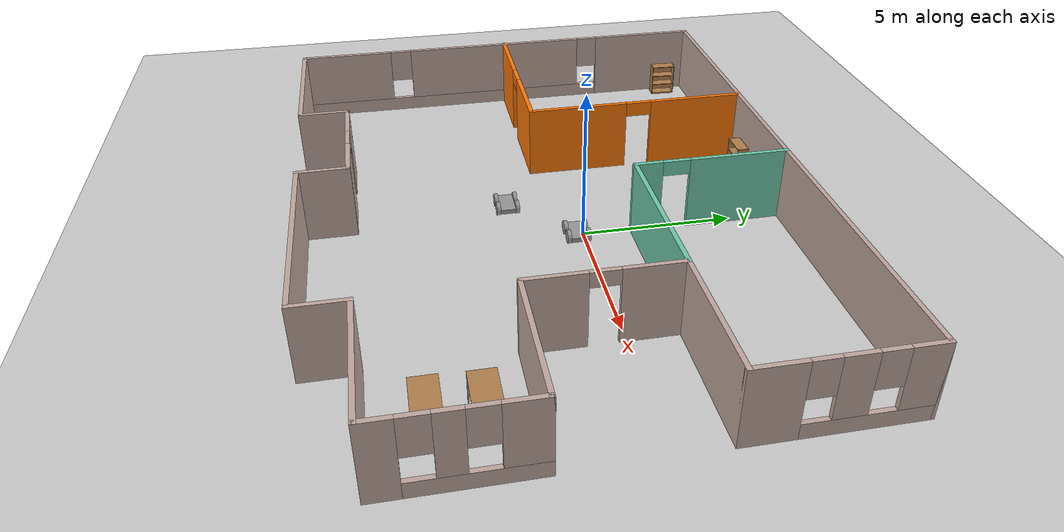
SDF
<sdf version="1.6">
 <world name="default">
  <plugin name="hello" filename="libhello.so"/>
  <light name="sun" type="directional">
   <pose>0 0 10 0 -0 0</pose>
   <diffuse>0.8 0.8 0.8 1</diffuse>
   <specular>0.2 0.2 0.2 1</specular>
   <attenuation>
    <range>1000</range>
    <constant>0.9</constant>
    <linear>0.01</linear>
    <quadratic>0.001</quadratic>
   </attenuation>
   <direction>-0.5 0.1 -0.9</direction>
  </light>
  <model name="ground_plane">
   <static>1</static>
   <link name="link">
    <collision name="collision">
     <geometry><plane><normal>0 0 1</normal><size>100 100</size></plane></geometry>
     <surface>
      <contact><collide_bitmask>65535</collide_bitmask></contact>
      <friction><ode><mu>100</mu><mu2>50</mu2></ode></friction>
     </surface>
    </collision>
    <visual name="visual">
     <cast_shadows>0</cast_shadows>
     <geometry><plane><normal>0 0 1</normal><size>100 100</size></plane></geometry>
     <material>
      <script><uri>file://media/materials/scripts/gazebo.material</uri><name>Gazebo/Grey</name></script>
     </material>
    </visual>
   </link>
  </model>
  <gravity>0 0 -9.8</gravity>
  <magnetic_field>6e-06 2.3e-05 -4.2e-05</magnetic_field>
  <atmosphere type="adiabatic"/>
  <physics name="default_physics" default="0" type="ode">
   <max_step_size>0.001</max_step_size>
   <real_time_factor>1</real_time_factor>
   <real_time_update_rate>1000</real_time_update_rate>
  </physics>
  <scene><ambient>0.4 0.4 0.4 1</ambient><background>0.7 0.7 0.7 1</background><shadows>1</shadows></scene>
  <spherical_coordinates>
   <surface_model>EARTH_WGS84</surface_model>
   <latitude_deg>0</latitude_deg>
   <longitude_deg>0</longitude_deg>
   <elevation>0</elevation>
   <heading_deg>0</heading_deg>
  </spherical_coordinates>
  <model name="bookshelf_2">
   <static>1</static>
   <link name="link">
    <inertial><mass>1</mass></inertial>
    <collision name="back">
     <pose>0 0.005 0.6 0 -0 0</pose>
     <geometry><box><size>0.9 0.01 1.2</size></box></geometry>
    </collision>
    <visual name="visual1">
     <pose>0 0.005 0.6 0 -0 0</pose>
     <geometry><box><size>0.9 0.01 1.2</size></box></geometry>
     <material>
      <script><uri>file://media/materials/scripts/gazebo.material</uri><name>Gazebo/Wood</name></script>
     </material>
    </visual>
    <collision name="left_side">
     <pose>0.45 -0.195 0.6 0 -0 0</pose>
     <geometry><box><size>0.02 0.4 1.2</size></box></geometry>
    </collision>
    <visual name="visual2">
     <pose>0.45 -0.195 0.6 0 -0 0</pose>
     <geometry><box><size>0.02 0.4 1.2</size></box></geometry>
     <material>
      <script><uri>file://media/materials/scripts/gazebo.material</uri><name>Gazebo/Wood</name></script>
     </material>
    </visual>
    <collision name="right_side">
     <pose>-0.45 -0.195 0.6 0 -0 0</pose>
     <geometry><box><size>0.02 0.4 1.2</size></box></geometry>
    </collision>
    <visual name="visual3">
     <pose>-0.45 -0.195 0.6 0 -0 0</pose>
     <geometry><box><size>0.02 0.4 1.2</size></box></geometry>
     <material>
      <script><uri>file://media/materials/scripts/gazebo.material</uri><name>Gazebo/Wood</name></script>
     </material>
    </visual>
    <collision name="bottom">
     <pose>0 -0.195 0.03 0 -0 0</pose>
     <geometry><box><size>0.88 0.4 0.06</size></box></geometry>
    </collision>
    <visual name="visual4">
     <pose>0 -0.195 0.03 0 -0 0</pose>
     <geometry><box><size>0.88 0.4 0.06</size></box></geometry>
     <material>
      <script><uri>file://media/materials/scripts/gazebo.material</uri><name>Gazebo/Wood</name></script>
     </material>
    </visual>
    <collision name="top">
     <pose>0 -0.195 1.19 0 -0 0</pose>
     <geometry><box><size>0.88 0.4 0.02</size></box></geometry>
    </collision>
    <visual name="visual5">
     <pose>0 -0.195 1.19 0 -0 0</pose>
     <geometry><box><size>0.88 0.4 0.02</size></box></geometry>
     <material>
      <script><uri>file://media/materials/scripts/gazebo.material</uri><name>Gazebo/Wood</name></script>
     </material>
    </visual>
    <collision name="low_shelf">
     <pose>0 -0.195 0.43 0 -0 0</pose>
     <geometry><box><size>0.88 0.4 0.02</size></box></geometry>
    </collision>
    <visual name="visual6">
     <pose>0 -0.195 0.43 0 -0 0</pose>
     <geometry><box><size>0.88 0.4 0.02</size></box></geometry>
     <material>
      <script><uri>file://media/materials/scripts/gazebo.material</uri><name>Gazebo/Wood</name></script>
     </material>
    </visual>
    <collision name="high_shelf">
     <pose>0 -0.195 0.8 0 -0 0</pose>
     <geometry><box><size>0.88 0.4 0.02</size></box></geometry>
    </collision>
    <visual name="visual7">
     <pose>0 -0.195 0.8 0 -0 0</pose>
     <geometry><box><size>0.88 0.4 0.02</size></box></geometry>
     <material>
      <script><uri>file://media/materials/scripts/gazebo.material</uri><name>Gazebo/Wood</name></script>
     </material>
    </visual>
   </link>
   <pose>-2.89056 6.54728 0 0 -0 0</pose>
  </model>
  <model name="bookshelf">
   <static>1</static>
   <link name="link">
    <inertial><mass>1</mass></inertial>
    <collision name="back">
     <pose>0 0.005 0.6 0 -0 0</pose>
     <geometry><box><size>0.9 0.01 1.2</size></box></geometry>
    </collision>
    <visual name="visual1">
     <pose>0 0.005 0.6 0 -0 0</pose>
     <geometry><box><size>0.9 0.01 1.2</size></box></geometry>
     <material>
      <script><uri>file://media/materials/scripts/gazebo.material</uri><name>Gazebo/Wood</name></script>
     </material>
    </visual>
    <collision name="left_side">
     <pose>0.45 -0.195 0.6 0 -0 0</pose>
     <geometry><box><size>0.02 0.4 1.2</size></box></geometry>
    </collision>
    <visual name="visual2">
     <pose>0.45 -0.195 0.6 0 -0 0</pose>
     <geometry><box><size>0.02 0.4 1.2</size></box></geometry>
     <material>
      <script><uri>file://media/materials/scripts/gazebo.material</uri><name>Gazebo/Wood</name></script>
     </material>
    </visual>
    <collision name="right_side">
     <pose>-0.45 -0.195 0.6 0 -0 0</pose>
     <geometry><box><size>0.02 0.4 1.2</size></box></geometry>
    </collision>
    <visual name="visual3">
     <pose>-0.45 -0.195 0.6 0 -0 0</pose>
     <geometry><box><size>0.02 0.4 1.2</size></box></geometry>
     <material>
      <script><uri>file://media/materials/scripts/gazebo.material</uri><name>Gazebo/Wood</name></script>
     </material>
    </visual>
    <collision name="bottom">
     <pose>0 -0.195 0.03 0 -0 0</pose>
     <geometry><box><size>0.88 0.4 0.06</size></box></geometry>
    </collision>
    <visual name="visual4">
     <pose>0 -0.195 0.03 0 -0 0</pose>
     <geometry><box><size>0.88 0.4 0.06</size></box></geometry>
     <material>
      <script><uri>file://media/materials/scripts/gazebo.material</uri><name>Gazebo/Wood</name></script>
     </material>
    </visual>
    <collision name="top">
     <pose>0 -0.195 1.19 0 -0 0</pose>
     <geometry><box><size>0.88 0.4 0.02</size></box></geometry>
    </collision>
    <visual name="visual5">
     <pose>0 -0.195 1.19 0 -0 0</pose>
     <geometry><box><size>0.88 0.4 0.02</size></box></geometry>
     <material>
      <script><uri>file://media/materials/scripts/gazebo.material</uri><name>Gazebo/Wood</name></script>
     </material>
    </visual>
    <collision name="low_shelf">
     <pose>0 -0.195 0.43 0 -0 0</pose>
     <geometry><box><size>0.88 0.4 0.02</size></box></geometry>
    </collision>
    <visual name="visual6">
     <pose>0 -0.195 0.43 0 -0 0</pose>
     <geometry><box><size>0.88 0.4 0.02</size></box></geometry>
     <material>
      <script><uri>file://media/materials/scripts/gazebo.material</uri><name>Gazebo/Wood</name></script>
     </material>
    </visual>
    <collision name="high_shelf">
     <pose>0 -0.195 0.8 0 -0 0</pose>
     <geometry><box><size>0.88 0.4 0.02</size></box></geometry>
    </collision>
    <visual name="visual7">
     <pose>0 -0.195 0.8 0 -0 0</pose>
     <geometry><box><size>0.88 0.4 0.02</size></box></geometry>
     <material>
      <script><uri>file://media/materials/scripts/gazebo.material</uri><name>Gazebo/Wood</name></script>
     </material>
    </visual>
   </link>
   <pose>-1.31133 6.55446 0 0 -0 0</pose>
  </model>
  <model name="bookshelf_0">
   <static>1</static>
   <link name="link">
    <inertial><mass>1</mass></inertial>
    <collision name="back">
     <pose>0 0.005 0.6 0 -0 0</pose>
     <geometry><box><size>0.9 0.01 1.2</size></box></geometry>
    </collision>
    <visual name="visual1">
     <pose>0 0.005 0.6 0 -0 0</pose>
     <geometry><box><size>0.9 0.01 1.2</size></box></geometry>
     <material>
      <script><uri>file://media/materials/scripts/gazebo.material</uri><name>Gazebo/Wood</name></script>
     </material>
    </visual>
    <collision name="left_side">
     <pose>0.45 -0.195 0.6 0 -0 0</pose>
     <geometry><box><size>0.02 0.4 1.2</size></box></geometry>
    </collision>
    <visual name="visual2">
     <pose>0.45 -0.195 0.6 0 -0 0</pose>
     <geometry><box><size>0.02 0.4 1.2</size></box></geometry>
     <material>
      <script><uri>file://media/materials/scripts/gazebo.material</uri><name>Gazebo/Wood</name></script>
     </material>
    </visual>
    <collision name="right_side">
     <pose>-0.45 -0.195 0.6 0 -0 0</pose>
     <geometry><box><size>0.02 0.4 1.2</size></box></geometry>
    </collision>
    <visual name="visual3">
     <pose>-0.45 -0.195 0.6 0 -0 0</pose>
     <geometry><box><size>0.02 0.4 1.2</size></box></geometry>
     <material>
      <script><uri>file://media/materials/scripts/gazebo.material</uri><name>Gazebo/Wood</name></script>
     </material>
    </visual>
    <collision name="bottom">
     <pose>0 -0.195 0.03 0 -0 0</pose>
     <geometry><box><size>0.88 0.4 0.06</size></box></geometry>
    </collision>
    <visual name="visual4">
     <pose>0 -0.195 0.03 0 -0 0</pose>
     <geometry><box><size>0.88 0.4 0.06</size></box></geometry>
     <material>
      <script><uri>file://media/materials/scripts/gazebo.material</uri><name>Gazebo/Wood</name></script>
     </material>
    </visual>
    <collision name="top">
     <pose>0 -0.195 1.19 0 -0 0</pose>
     <geometry><box><size>0.88 0.4 0.02</size></box></geometry>
    </collision>
    <visual name="visual5">
     <pose>0 -0.195 1.19 0 -0 0</pose>
     <geometry><box><size>0.88 0.4 0.02</size></box></geometry>
     <material>
      <script><uri>file://media/materials/scripts/gazebo.material</uri><name>Gazebo/Wood</name></script>
     </material>
    </visual>
    <collision name="low_shelf">
     <pose>0 -0.195 0.43 0 -0 0</pose>
     <geometry><box><size>0.88 0.4 0.02</size></box></geometry>
    </collision>
    <visual name="visual6">
     <pose>0 -0.195 0.43 0 -0 0</pose>
     <geometry><box><size>0.88 0.4 0.02</size></box></geometry>
     <material>
      <script><uri>file://media/materials/scripts/gazebo.material</uri><name>Gazebo/Wood</name></script>
     </material>
    </visual>
    <collision name="high_shelf">
     <pose>0 -0.195 0.8 0 -0 0</pose>
     <geometry><box><size>0.88 0.4 0.02</size></box></geometry>
    </collision>
    <visual name="visual7">
     <pose>0 -0.195 0.8 0 -0 0</pose>
     <geometry><box><size>0.88 0.4 0.02</size></box></geometry>
     <material>
      <script><uri>file://media/materials/scripts/gazebo.material</uri><name>Gazebo/Wood</name></script>
     </material>
    </visual>
   </link>
   <pose>-10.3656 5.7332 0 0 -0 1.52719</pose>
  </model>
  <model name="table">
   <static>1</static>
   <link name="link">
    <collision name="surface">
     <pose>0 0 1 0 -0 0</pose>
     <geometry><box><size>1.5 0.8 0.03</size></box></geometry>
     <surface><friction><ode><mu>0.6</mu><mu2>0.6</mu2></ode></friction></surface>
    </collision>
    <visual name="visual1">
     <pose>0 0 1 0 -0 0</pose>
     <geometry><box><size>1.5 0.8 0.03</size></box></geometry>
     <material>
      <script><uri>file://media/materials/scripts/gazebo.material</uri><name>Gazebo/Wood</name></script>
     </material>
    </visual>
    <collision name="front_left_leg">
     <pose>0.68 0.38 0.5 0 -0 0</pose>
     <geometry><cylinder><radius>0.02</radius><length>1</length></cylinder></geometry>
    </collision>
    <visual name="front_left_leg">
     <pose>0.68 0.38 0.5 0 -0 0</pose>
     <geometry><cylinder><radius>0.02</radius><length>1</length></cylinder></geometry>
     <material>
      <script><uri>file://media/materials/scripts/gazebo.material</uri><name>Gazebo/Grey</name></script>
     </material>
    </visual>
    <collision name="front_right_leg">
     <pose>0.68 -0.38 0.5 0 -0 0</pose>
     <geometry><cylinder><radius>0.02</radius><length>1</length></cylinder></geometry>
    </collision>
    <visual name="front_right_leg">
     <pose>0.68 -0.38 0.5 0 -0 0</pose>
     <geometry><cylinder><radius>0.02</radius><length>1</length></cylinder></geometry>
     <material>
      <script><uri>file://media/materials/scripts/gazebo.material</uri><name>Gazebo/Grey</name></script>
     </material>
    </visual>
    <collision name="back_right_leg">
     <pose>-0.68 -0.38 0.5 0 -0 0</pose>
     <geometry><cylinder><radius>0.02</radius><length>1</length></cylinder></geometry>
    </collision>
    <visual name="back_right_leg">
     <pose>-0.68 -0.38 0.5 0 -0 0</pose>
     <geometry><cylinder><radius>0.02</radius><length>1</length></cylinder></geometry>
     <material>
      <script><uri>file://media/materials/scripts/gazebo.material</uri><name>Gazebo/Grey</name></script>
     </material>
    </visual>
    <collision name="back_left_leg">
     <pose>-0.68 0.38 0.5 0 -0 0</pose>
     <geometry><cylinder><radius>0.02</radius><length>1</length></cylinder></geometry>
    </collision>
    <visual name="back_left_leg">
     <pose>-0.68 0.38 0.5 0 -0 0</pose>
     <geometry><cylinder><radius>0.02</radius><length>1</length></cylinder></geometry>
     <material>
      <script><uri>file://media/materials/scripts/gazebo.material</uri><name>Gazebo/Grey</name></script>
     </material>
    </visual>
   </link>
   <pose>7.74226 -4.23581 0 0 -0 0</pose>
  </model>
  <model name="table_0">
   <static>1</static>
   <link name="link">
    <collision name="surface">
     <pose>0 0 1 0 -0 0</pose>
     <geometry><box><size>1.5 0.8 0.03</size></box></geometry>
     <surface><friction><ode><mu>0.6</mu><mu2>0.6</mu2></ode></friction></surface>
    </collision>
    <visual name="visual1">
     <pose>0 0 1 0 -0 0</pose>
     <geometry><box><size>1.5 0.8 0.03</size></box></geometry>
     <material>
      <script><uri>file://media/materials/scripts/gazebo.material</uri><name>Gazebo/Wood</name></script>
     </material>
    </visual>
    <collision name="front_left_leg">
     <pose>0.68 0.38 0.5 0 -0 0</pose>
     <geometry><cylinder><radius>0.02</radius><length>1</length></cylinder></geometry>
    </collision>
    <visual name="front_left_leg">
     <pose>0.68 0.38 0.5 0 -0 0</pose>
     <geometry><cylinder><radius>0.02</radius><length>1</length></cylinder></geometry>
     <material>
      <script><uri>file://media/materials/scripts/gazebo.material</uri><name>Gazebo/Grey</name></script>
     </material>
    </visual>
    <collision name="front_right_leg">
     <pose>0.68 -0.38 0.5 0 -0 0</pose>
     <geometry><cylinder><radius>0.02</radius><length>1</length></cylinder></geometry>
    </collision>
    <visual name="front_right_leg">
     <pose>0.68 -0.38 0.5 0 -0 0</pose>
     <geometry><cylinder><radius>0.02</radius><length>1</length></cylinder></geometry>
     <material>
      <script><uri>file://media/materials/scripts/gazebo.material</uri><name>Gazebo/Grey</name></script>
     </material>
    </visual>
    <collision name="back_right_leg">
     <pose>-0.68 -0.38 0.5 0 -0 0</pose>
     <geometry><cylinder><radius>0.02</radius><length>1</length></cylinder></geometry>
    </collision>
    <visual name="back_right_leg">
     <pose>-0.68 -0.38 0.5 0 -0 0</pose>
     <geometry><cylinder><radius>0.02</radius><length>1</length></cylinder></geometry>
     <material>
      <script><uri>file://media/materials/scripts/gazebo.material</uri><name>Gazebo/Grey</name></script>
     </material>
    </visual>
    <collision name="back_left_leg">
     <pose>-0.68 0.38 0.5 0 -0 0</pose>
     <geometry><cylinder><radius>0.02</radius><length>1</length></cylinder></geometry>
    </collision>
    <visual name="back_left_leg">
     <pose>-0.68 0.38 0.5 0 -0 0</pose>
     <geometry><cylinder><radius>0.02</radius><length>1</length></cylinder></geometry>
     <material>
      <script><uri>file://media/materials/scripts/gazebo.material</uri><name>Gazebo/Grey</name></script>
     </material>
    </visual>
   </link>
   <pose>7.69183 -5.72226 0 0 -0 0</pose>
  </model>
  <model name="Office">
   <pose>-0.4312 -1.09674 0 0 -0 0</pose>
   <link name="Wall_12">
    <pose>-10.1892 -0.024999 0 0 0 -1.5708</pose>
    <visual name="Wall_12_Visual_0">
     <pose>-5.93121 0 1.25 0 -0 0</pose>
     <geometry><box><size>3.88759 0.15 2.5</size></box></geometry>
     <material>
      <script><uri>file://media/materials/scripts/gazebo.material</uri><name>Gazebo/Grey</name></script>
      <ambient>0.760784 0.662745 0.627451 1</ambient>
     </material>
     <meta><layer>0</layer></meta>
    </visual>
    <collision name="Wall_12_Collision_0">
     <geometry><box><size>3.88759 0.15 2.5</size></box></geometry>
     <pose>-5.93121 0 1.25 0 -0 0</pose>
    </collision>
    <visual name="Wall_12_Visual_1">
     <pose>1.94379 0 0.25 0 -0 0</pose>
     <geometry><box><size>11.8624 0.15 0.5</size></box></geometry>
     <material>
      <script><uri>file://media/materials/scripts/gazebo.material</uri><name>Gazebo/Grey</name></script>
      <ambient>0.760784 0.662745 0.627451 1</ambient>
     </material>
     <meta><layer>0</layer></meta>
    </visual>
    <collision name="Wall_12_Collision_1">
     <geometry><box><size>11.8624 0.15 0.5</size></box></geometry>
     <pose>1.94379 0 0.25 0 -0 0</pose>
    </collision>
    <visual name="Wall_12_Visual_2">
     <pose>0.229137 0 1.5 0 -0 0</pose>
     <geometry><box><size>6.8331 0.15 2</size></box></geometry>
     <material>
      <script><uri>file://media/materials/scripts/gazebo.material</uri><name>Gazebo/Grey</name></script>
      <ambient>0.760784 0.662745 0.627451 1</ambient>
     </material>
     <meta><layer>0</layer></meta>
    </visual>
    <collision name="Wall_12_Collision_2">
     <geometry><box><size>6.8331 0.15 2</size></box></geometry>
     <pose>0.229137 0 1.5 0 -0 0</pose>
    </collision>
    <visual name="Wall_12_Visual_3">
     <pose>6.16034 0 1.5 0 -0 0</pose>
     <geometry><box><size>3.42931 0.15 2</size></box></geometry>
     <material>
      <script><uri>file://media/materials/scripts/gazebo.material</uri><name>Gazebo/Grey</name></script>
      <ambient>0.760784 0.662745 0.627451 1</ambient>
     </material>
     <meta><layer>0</layer></meta>
    </visual>
    <collision name="Wall_12_Collision_3">
     <geometry><box><size>3.42931 0.15 2</size></box></geometry>
     <pose>6.16034 0 1.5 0 -0 0</pose>
    </collision>
    <visual name="Wall_12_Visual_4">
     <pose>-3.58741 0 1.9 0 -0 0</pose>
     <geometry><box><size>0.8 0.15 1.2</size></box></geometry>
     <material>
      <script><uri>file://media/materials/scripts/gazebo.material</uri><name>Gazebo/Grey</name></script>
      <ambient>0.760784 0.662745 0.627451 1</ambient>
     </material>
     <meta><layer>0</layer></meta>
    </visual>
    <collision name="Wall_12_Collision_4">
     <geometry><box><size>0.8 0.15 1.2</size></box></geometry>
     <pose>-3.58741 0 1.9 0 -0 0</pose>
    </collision>
    <visual name="Wall_12_Visual_5">
     <pose>4.04569 0 1.9 0 -0 0</pose>
     <geometry><box><size>0.8 0.15 1.2</size></box></geometry>
     <material>
      <script><uri>file://media/materials/scripts/gazebo.material</uri><name>Gazebo/Grey</name></script>
      <ambient>0.760784 0.662745 0.627451 1</ambient>
     </material>
     <meta><layer>0</layer></meta>
    </visual>
    <collision name="Wall_12_Collision_5">
     <geometry><box><size>0.8 0.15 1.2</size></box></geometry>
     <pose>4.04569 0 1.9 0 -0 0</pose>
    </collision>
   </link>
   <link name="Wall_13">
    <collision name="Wall_13_Collision">
     <geometry><box><size>5.25 0.15 2.5</size></box></geometry>
     <pose>0 0 1.25 0 -0 0</pose>
    </collision>
    <visual name="Wall_13_Visual">
     <pose>0 0 1.25 0 -0 0</pose>
     <geometry><box><size>5.25 0.15 2.5</size></box></geometry>
     <material>
      <script><uri>file://media/materials/scripts/gazebo.material</uri><name>Gazebo/Grey</name></script>
      <ambient>0.760784 0.662745 0.627451 1</ambient>
     </material>
     <meta><layer>0</layer></meta>
    </visual>
    <pose>-7.63921 -7.825 0 0 -0 0</pose>
   </link>
   <link name="Wall_14">
    <collision name="Wall_14_Collision">
     <geometry><box><size>1.75 0.15 2.5</size></box></geometry>
     <pose>0 0 1.25 0 -0 0</pose>
    </collision>
    <visual name="Wall_14_Visual">
     <pose>0 0 1.25 0 -0 0</pose>
     <geometry><box><size>1.75 0.15 2.5</size></box></geometry>
     <material>
      <script><uri>file://media/materials/scripts/gazebo.material</uri><name>Gazebo/Grey</name></script>
      <ambient>0.760784 0.662745 0.627451 1</ambient>
     </material>
     <meta><layer>0</layer></meta>
    </visual>
    <pose>-5.08921 -7.025 0 0 -0 1.5708</pose>
   </link>
   <link name="Wall_15">
    <pose>-3.03921 -6.225 0 0 -0 0</pose>
    <visual name="Wall_15_Visual_0">
     <pose>-1.30944 0 1.25 0 -0 0</pose>
     <geometry><box><size>1.63111 0.15 2.5</size></box></geometry>
     <material>
      <script><uri>file://media/materials/scripts/gazebo.material</uri><name>Gazebo/Grey</name></script>
      <ambient>0.760784 0.662745 0.627451 1</ambient>
     </material>
     <meta><layer>0</layer></meta>
    </visual>
    <collision name="Wall_15_Collision_0">
     <geometry><box><size>1.63111 0.15 2.5</size></box></geometry>
     <pose>-1.30944 0 1.25 0 -0 0</pose>
    </collision>
    <visual name="Wall_15_Visual_1">
     <pose>1.26555 0 1.25 0 -0 0</pose>
     <geometry><box><size>1.71889 0.15 2.5</size></box></geometry>
     <material>
      <script><uri>file://media/materials/scripts/gazebo.material</uri><name>Gazebo/Grey</name></script>
      <ambient>0.760784 0.662745 0.627451 1</ambient>
     </material>
     <meta><layer>0</layer></meta>
    </visual>
    <collision name="Wall_15_Collision_1">
     <geometry><box><size>1.71889 0.15 2.5</size></box></geometry>
     <pose>1.26555 0 1.25 0 -0 0</pose>
    </collision>
    <visual name="Wall_15_Visual_2">
     <pose>-0.04389 0 2.25 0 -0 0</pose>
     <geometry><box><size>0.9 0.15 0.5</size></box></geometry>
     <material>
      <script><uri>file://media/materials/scripts/gazebo.material</uri><name>Gazebo/Grey</name></script>
      <ambient>0.760784 0.662745 0.627451 1</ambient>
     </material>
     <meta><layer>0</layer></meta>
    </visual>
    <collision name="Wall_15_Collision_2">
     <geometry><box><size>0.9 0.15 0.5</size></box></geometry>
     <pose>-0.04389 0 2.25 0 -0 0</pose>
    </collision>
   </link>
   <link name="Wall_16">
    <collision name="Wall_16_Collision">
     <geometry><box><size>1.75 0.15 2.5</size></box></geometry>
     <pose>0 0 1.25 0 -0 0</pose>
    </collision>
    <visual name="Wall_16_Visual">
     <pose>0 0 1.25 0 -0 0</pose>
     <geometry><box><size>1.75 0.15 2.5</size></box></geometry>
     <material>
      <script><uri>file://media/materials/scripts/gazebo.material</uri><name>Gazebo/Grey</name></script>
      <ambient>0.760784 0.662745 0.627451 1</ambient>
     </material>
     <meta><layer>0</layer></meta>
    </visual>
    <pose>-0.98921 -7.025 0 0 0 -1.5708</pose>
   </link>
   <link name="Wall_17">
    <collision name="Wall_17_Collision">
     <geometry><box><size>7 0.15 2.5</size></box></geometry>
     <pose>0 0 1.25 0 -0 0</pose>
    </collision>
    <visual name="Wall_17_Visual">
     <pose>0 0 1.25 0 -0 0</pose>
     <geometry><box><size>7 0.15 2.5</size></box></geometry>
     <material>
      <script><uri>file://media/materials/scripts/gazebo.material</uri><name>Gazebo/Grey</name></script>
      <ambient>0.760784 0.662745 0.627451 1</ambient>
     </material>
     <meta><layer>0</layer></meta>
    </visual>
    <pose>2.43579 -7.825 0 0 -0 0</pose>
   </link>
   <link name="Wall_18">
    <collision name="Wall_18_Collision">
     <geometry><box><size>1.75 0.15 2.5</size></box></geometry>
     <pose>0 0 1.25 0 -0 0</pose>
    </collision>
    <visual name="Wall_18_Visual">
     <pose>0 0 1.25 0 -0 0</pose>
     <geometry><box><size>1.75 0.15 2.5</size></box></geometry>
     <material>
      <script><uri>file://media/materials/scripts/gazebo.material</uri><name>Gazebo/Grey</name></script>
      <ambient>0.760784 0.662745 0.627451 1</ambient>
     </material>
     <meta><layer>0</layer></meta>
    </visual>
    <pose>5.86079 -7.025 0 0 -0 1.5708</pose>
   </link>
   <link name="Wall_19">
    <collision name="Wall_19_Collision">
     <geometry><box><size>4.5 0.15 2.5</size></box></geometry>
     <pose>0 0 1.25 0 -0 0</pose>
    </collision>
    <visual name="Wall_19_Visual">
     <pose>0 0 1.25 0 -0 0</pose>
     <geometry><box><size>4.5 0.15 2.5</size></box></geometry>
     <material>
      <script><uri>file://media/materials/scripts/gazebo.material</uri><name>Gazebo/Grey</name></script>
      <ambient>0.760784 0.662745 0.627451 1</ambient>
     </material>
     <meta><layer>0</layer></meta>
    </visual>
    <pose>8.03579 -6.225 0 0 -0 0</pose>
   </link>
   <link name="Wall_20">
    <pose>10.2108 -4.05 0 0 -0 1.5708</pose>
    <visual name="Wall_20_Visual_0">
     <pose>-1.77798 0 1.25 0 -0 0</pose>
     <geometry><box><size>0.944037 0.15 2.5</size></box></geometry>
     <material>
      <script><uri>file://media/materials/scripts/gazebo.material</uri><name>Gazebo/Grey</name></script>
      <ambient>0.760784 0.662745 0.627451 1</ambient>
     </material>
     <meta><layer>0</layer></meta>
    </visual>
    <collision name="Wall_20_Collision_0">
     <geometry><box><size>0.944037 0.15 2.5</size></box></geometry>
     <pose>-1.77798 0 1.25 0 -0 0</pose>
    </collision>
    <visual name="Wall_20_Visual_1">
     <pose>0.472018 0 0.25 0 -0 0</pose>
     <geometry><box><size>3.55596 0.15 0.5</size></box></geometry>
     <material>
      <script><uri>file://media/materials/scripts/gazebo.material</uri><name>Gazebo/Grey</name></script>
      <ambient>0.760784 0.662745 0.627451 1</ambient>
     </material>
     <meta><layer>0</layer></meta>
    </visual>
    <collision name="Wall_20_Collision_1">
     <geometry><box><size>3.55596 0.15 0.5</size></box></geometry>
     <pose>0.472018 0 0.25 0 -0 0</pose>
    </collision>
    <visual name="Wall_20_Visual_2">
     <pose>-0.132031 0 1.5 0 -0 0</pose>
     <geometry><box><size>0.747865 0.15 2</size></box></geometry>
     <material>
      <script><uri>file://media/materials/scripts/gazebo.material</uri><name>Gazebo/Grey</name></script>
      <ambient>0.760784 0.662745 0.627451 1</ambient>
     </material>
     <meta><layer>0</layer></meta>
    </visual>
    <collision name="Wall_20_Collision_2">
     <geometry><box><size>0.747865 0.15 2</size></box></geometry>
     <pose>-0.132031 0 1.5 0 -0 0</pose>
    </collision>
    <visual name="Wall_20_Visual_3">
     <pose>1.64595 0 1.5 0 -0 0</pose>
     <geometry><box><size>1.2081 0.15 2</size></box></geometry>
     <material>
      <script><uri>file://media/materials/scripts/gazebo.material</uri><name>Gazebo/Grey</name></script>
      <ambient>0.760784 0.662745 0.627451 1</ambient>
     </material>
     <meta><layer>0</layer></meta>
    </visual>
    <collision name="Wall_20_Collision_3">
     <geometry><box><size>1.2081 0.15 2</size></box></geometry>
     <pose>1.64595 0 1.5 0 -0 0</pose>
    </collision>
    <visual name="Wall_20_Visual_4">
     <pose>-0.905963 0 1.9 0 -0 0</pose>
     <geometry><box><size>0.8 0.15 1.2</size></box></geometry>
     <material>
      <script><uri>file://media/materials/scripts/gazebo.material</uri><name>Gazebo/Grey</name></script>
      <ambient>0.760784 0.662745 0.627451 1</ambient>
     </material>
     <meta><layer>0</layer></meta>
    </visual>
    <collision name="Wall_20_Collision_4">
     <geometry><box><size>0.8 0.15 1.2</size></box></geometry>
     <pose>-0.905963 0 1.9 0 -0 0</pose>
    </collision>
    <visual name="Wall_20_Visual_5">
     <pose>0.641902 0 1.9 0 -0 0</pose>
     <geometry><box><size>0.8 0.15 1.2</size></box></geometry>
     <material>
      <script><uri>file://media/materials/scripts/gazebo.material</uri><name>Gazebo/Grey</name></script>
      <ambient>0.760784 0.662745 0.627451 1</ambient>
     </material>
     <meta><layer>0</layer></meta>
    </visual>
    <collision name="Wall_20_Collision_5">
     <geometry><box><size>0.8 0.15 1.2</size></box></geometry>
     <pose>0.641902 0 1.9 0 -0 0</pose>
    </collision>
   </link>
   <link name="Wall_21">
    <collision name="Wall_21_Collision">
     <geometry><box><size>4.5 0.15 2.5</size></box></geometry>
     <pose>0 0 1.25 0 -0 0</pose>
    </collision>
    <visual name="Wall_21_Visual">
     <pose>0 0 1.25 0 -0 0</pose>
     <geometry><box><size>4.5 0.15 2.5</size></box></geometry>
     <material>
      <script><uri>file://media/materials/scripts/gazebo.material</uri><name>Gazebo/Grey</name></script>
      <ambient>0.760784 0.662745 0.627451 1</ambient>
     </material>
     <meta><layer>0</layer></meta>
    </visual>
    <pose>8.03579 -1.875 0 0 -0 3.14159</pose>
   </link>
   <link name="Wall_22">
    <pose>5.86079 0.425001 0 0 -0 1.5708</pose>
    <visual name="Wall_22_Visual_0">
     <pose>-1.41181 0 1.25 0 -0 0</pose>
     <geometry><box><size>1.92639 0.15 2.5</size></box></geometry>
     <material>
      <script><uri>file://media/materials/scripts/gazebo.material</uri><name>Gazebo/Grey</name></script>
      <ambient>0.760784 0.662745 0.627451 1</ambient>
     </material>
     <meta><layer>0</layer></meta>
    </visual>
    <collision name="Wall_22_Collision_0">
     <geometry><box><size>1.92639 0.15 2.5</size></box></geometry>
     <pose>-1.41181 0 1.25 0 -0 0</pose>
    </collision>
    <visual name="Wall_22_Visual_1">
     <pose>1.41319 0 1.25 0 -0 0</pose>
     <geometry><box><size>1.92361 0.15 2.5</size></box></geometry>
     <material>
      <script><uri>file://media/materials/scripts/gazebo.material</uri><name>Gazebo/Grey</name></script>
      <ambient>0.760784 0.662745 0.627451 1</ambient>
     </material>
     <meta><layer>0</layer></meta>
    </visual>
    <collision name="Wall_22_Collision_1">
     <geometry><box><size>1.92361 0.15 2.5</size></box></geometry>
     <pose>1.41319 0 1.25 0 -0 0</pose>
    </collision>
    <visual name="Wall_22_Visual_2">
     <pose>0.001387 0 2.25 0 -0 0</pose>
     <geometry><box><size>0.9 0.15 0.5</size></box></geometry>
     <material>
      <script><uri>file://media/materials/scripts/gazebo.material</uri><name>Gazebo/Grey</name></script>
      <ambient>0.760784 0.662745 0.627451 1</ambient>
     </material>
     <meta><layer>0</layer></meta>
    </visual>
    <collision name="Wall_22_Collision_2">
     <geometry><box><size>0.9 0.15 0.5</size></box></geometry>
     <pose>0.001387 0 2.25 0 -0 0</pose>
    </collision>
   </link>
   <link name="Wall_23">
    <collision name="Wall_23_Collision">
     <geometry><box><size>4.5 0.15 2.5</size></box></geometry>
     <pose>0 0 1.25 0 -0 0</pose>
    </collision>
    <visual name="Wall_23_Visual">
     <pose>0 0 1.25 0 -0 0</pose>
     <geometry><box><size>4.5 0.15 2.5</size></box></geometry>
     <material>
      <script><uri>file://media/materials/scripts/gazebo.material</uri><name>Gazebo/Grey</name></script>
      <ambient>0.760784 0.662745 0.627451 1</ambient>
     </material>
     <meta><layer>0</layer></meta>
    </visual>
    <pose>8.03579 2.725 0 0 -0 0</pose>
   </link>
   <link name="Wall_24">
    <pose>10.2108 5.275 0 0 -0 1.5708</pose>
    <visual name="Wall_24_Visual_0">
     <pose>-1.82608 0 1.25 0 -0 0</pose>
     <geometry><box><size>1.59784 0.15 2.5</size></box></geometry>
     <material>
      <script><uri>file://media/materials/scripts/gazebo.material</uri><name>Gazebo/Grey</name></script>
      <ambient>0.760784 0.662745 0.627451 1</ambient>
     </material>
     <meta><layer>0</layer></meta>
    </visual>
    <collision name="Wall_24_Collision_0">
     <geometry><box><size>1.59784 0.15 2.5</size></box></geometry>
     <pose>-1.82608 0 1.25 0 -0 0</pose>
    </collision>
    <visual name="Wall_24_Visual_1">
     <pose>0.798919 0 0.25 0 -0 0</pose>
     <geometry><box><size>3.65216 0.15 0.5</size></box></geometry>
     <material>
      <script><uri>file://media/materials/scripts/gazebo.material</uri><name>Gazebo/Grey</name></script>
      <ambient>0.760784 0.662745 0.627451 1</ambient>
     </material>
     <meta><layer>0</layer></meta>
    </visual>
    <collision name="Wall_24_Collision_1">
     <geometry><box><size>3.65216 0.15 0.5</size></box></geometry>
     <pose>0.798919 0 0.25 0 -0 0</pose>
    </collision>
    <visual name="Wall_24_Visual_2">
     <pose>0.252308 0 1.5 0 -0 0</pose>
     <geometry><box><size>0.958938 0.15 2</size></box></geometry>
     <material>
      <script><uri>file://media/materials/scripts/gazebo.material</uri><name>Gazebo/Grey</name></script>
      <ambient>0.760784 0.662745 0.627451 1</ambient>
     </material>
     <meta><layer>0</layer></meta>
    </visual>
    <collision name="Wall_24_Collision_2">
     <geometry><box><size>0.958938 0.15 2</size></box></geometry>
     <pose>0.252308 0 1.5 0 -0 0</pose>
    </collision>
    <visual name="Wall_24_Visual_3">
     <pose>2.07839 0 1.5 0 -0 0</pose>
     <geometry><box><size>1.09322 0.15 2</size></box></geometry>
     <material>
      <script><uri>file://media/materials/scripts/gazebo.material</uri><name>Gazebo/Grey</name></script>
      <ambient>0.760784 0.662745 0.627451 1</ambient>
     </material>
     <meta><layer>0</layer></meta>
    </visual>
    <collision name="Wall_24_Collision_3">
     <geometry><box><size>1.09322 0.15 2</size></box></geometry>
     <pose>2.07839 0 1.5 0 -0 0</pose>
    </collision>
    <visual name="Wall_24_Visual_4">
     <pose>-0.627161 0 1.9 0 -0 0</pose>
     <geometry><box><size>0.8 0.15 1.2</size></box></geometry>
     <material>
      <script><uri>file://media/materials/scripts/gazebo.material</uri><name>Gazebo/Grey</name></script>
      <ambient>0.760784 0.662745 0.627451 1</ambient>
     </material>
     <meta><layer>0</layer></meta>
    </visual>
    <collision name="Wall_24_Collision_4">
     <geometry><box><size>0.8 0.15 1.2</size></box></geometry>
     <pose>-0.627161 0 1.9 0 -0 0</pose>
    </collision>
    <visual name="Wall_24_Visual_5">
     <pose>1.13178 0 1.9 0 -0 0</pose>
     <geometry><box><size>0.8 0.15 1.2</size></box></geometry>
     <material>
      <script><uri>file://media/materials/scripts/gazebo.material</uri><name>Gazebo/Grey</name></script>
      <ambient>0.760784 0.662745 0.627451 1</ambient>
     </material>
     <meta><layer>0</layer></meta>
    </visual>
    <collision name="Wall_24_Collision_5">
     <geometry><box><size>0.8 0.15 1.2</size></box></geometry>
     <pose>1.13178 0 1.9 0 -0 0</pose>
    </collision>
   </link>
   <link name="Wall_25">
    <collision name="Wall_25_Collision">
     <geometry><box><size>20.5 0.15 2.5</size></box></geometry>
     <pose>0 0 1.25 0 -0 0</pose>
    </collision>
    <visual name="Wall_25_Visual">
     <pose>0 0 1.25 0 -0 0</pose>
     <geometry><box><size>20.5 0.15 2.5</size></box></geometry>
     <material>
      <script><uri>file://media/materials/scripts/gazebo.material</uri><name>Gazebo/Grey</name></script>
      <ambient>0.760784 0.662745 0.627451 1</ambient>
     </material>
     <meta><layer>0</layer></meta>
    </visual>
    <pose>0.03579 7.825 0 0 -0 3.14159</pose>
   </link>
   <link name="Wall_27">
    <pose>-7.03579 0.139084 0 0 -0 0</pose>
    <visual name="Wall_27_Visual_0">
     <pose>-1.87618 0 1.25 0 -0 0</pose>
     <geometry><box><size>2.74763 0.15 2.5</size></box></geometry>
     <material>
      <script><uri>file://media/materials/scripts/gazebo.material</uri><name>Gazebo/Grey</name></script>
      <ambient>0.996078 0.47451 0.0196078 1</ambient>
     </material>
     <meta><layer>0</layer></meta>
    </visual>
    <collision name="Wall_27_Collision_0">
     <geometry><box><size>2.74763 0.15 2.5</size></box></geometry>
     <pose>-1.87618 0 1.25 0 -0 0</pose>
    </collision>
    <visual name="Wall_27_Visual_1">
     <pose>1.82382 0 1.25 0 -0 0</pose>
     <geometry><box><size>2.85237 0.15 2.5</size></box></geometry>
     <material>
      <script><uri>file://media/materials/scripts/gazebo.material</uri><name>Gazebo/Grey</name></script>
      <ambient>0.996078 0.47451 0.0196078 1</ambient>
     </material>
     <meta><layer>0</layer></meta>
    </visual>
    <collision name="Wall_27_Collision_1">
     <geometry><box><size>2.85237 0.15 2.5</size></box></geometry>
     <pose>1.82382 0 1.25 0 -0 0</pose>
    </collision>
    <visual name="Wall_27_Visual_2">
     <pose>-0.052368 0 2.25 0 -0 0</pose>
     <geometry><box><size>0.9 0.15 0.5</size></box></geometry>
     <material>
      <script><uri>file://media/materials/scripts/gazebo.material</uri><name>Gazebo/Grey</name></script>
      <ambient>0.996078 0.47451 0.0196078 1</ambient>
     </material>
     <meta><layer>0</layer></meta>
    </visual>
    <collision name="Wall_27_Collision_2">
     <geometry><box><size>0.9 0.15 0.5</size></box></geometry>
     <pose>-0.052368 0 2.25 0 -0 0</pose>
    </collision>
   </link>
   <link name="Wall_28">
    <pose>-3.86079 3.93908 0 0 -0 1.5708</pose>
    <visual name="Wall_28_Visual_0">
     <pose>-2.10796 0 1.25 0 -0 0</pose>
     <geometry><box><size>3.53407 0.15 2.5</size></box></geometry>
     <material>
      <script><uri>file://media/materials/scripts/gazebo.material</uri><name>Gazebo/Grey</name></script>
      <ambient>0.996078 0.47451 0.0196078 1</ambient>
     </material>
     <meta><layer>0</layer></meta>
    </visual>
    <collision name="Wall_28_Collision_0">
     <geometry><box><size>3.53407 0.15 2.5</size></box></geometry>
     <pose>-2.10796 0 1.25 0 -0 0</pose>
    </collision>
    <visual name="Wall_28_Visual_1">
     <pose>2.21704 0 1.25 0 -0 0</pose>
     <geometry><box><size>3.31593 0.15 2.5</size></box></geometry>
     <material>
      <script><uri>file://media/materials/scripts/gazebo.material</uri><name>Gazebo/Grey</name></script>
      <ambient>0.996078 0.47451 0.0196078 1</ambient>
     </material>
     <meta><layer>0</layer></meta>
    </visual>
    <collision name="Wall_28_Collision_1">
     <geometry><box><size>3.31593 0.15 2.5</size></box></geometry>
     <pose>2.21704 0 1.25 0 -0 0</pose>
    </collision>
    <visual name="Wall_28_Visual_2">
     <pose>0.109073 0 2.25 0 -0 0</pose>
     <geometry><box><size>0.9 0.15 0.5</size></box></geometry>
     <material>
      <script><uri>file://media/materials/scripts/gazebo.material</uri><name>Gazebo/Grey</name></script>
      <ambient>0.996078 0.47451 0.0196078 1</ambient>
     </material>
     <meta><layer>0</layer></meta>
    </visual>
    <collision name="Wall_28_Collision_2">
     <geometry><box><size>0.9 0.15 0.5</size></box></geometry>
     <pose>0.109073 0 2.25 0 -0 0</pose>
    </collision>
   </link>
   <link name="Wall_30">
    <collision name="Wall_30_Collision">
     <geometry><box><size>5.5 0.15 2.5</size></box></geometry>
     <pose>0 0 1.25 0 -0 0</pose>
    </collision>
    <visual name="Wall_30_Visual">
     <pose>0 0 1.25 0 -0 0</pose>
     <geometry><box><size>5.5 0.15 2.5</size></box></geometry>
     <material>
      <script><uri>file://media/materials/scripts/gazebo.material</uri><name>Gazebo/Grey</name></script>
      <ambient>0.435294 0.796078 0.67451 1</ambient>
     </material>
     <meta><layer>0</layer></meta>
    </visual>
    <pose>3.18579 2.725 0 0 -0 3.14159</pose>
   </link>
   <link name="Wall_31">
    <pose>0.51079 5.275 0 0 -0 1.5708</pose>
    <visual name="Wall_31_Visual_0">
     <pose>-2.13099 0 1.25 0 -0 0</pose>
     <geometry><box><size>0.988014 0.15 2.5</size></box></geometry>
     <material>
      <script><uri>file://media/materials/scripts/gazebo.material</uri><name>Gazebo/Grey</name></script>
      <ambient>0.435294 0.796078 0.67451 1</ambient>
     </material>
     <meta><layer>0</layer></meta>
    </visual>
    <collision name="Wall_31_Collision_0">
     <geometry><box><size>0.988014 0.15 2.5</size></box></geometry>
     <pose>-2.13099 0 1.25 0 -0 0</pose>
    </collision>
    <visual name="Wall_31_Visual_1">
     <pose>0.944007 0 1.25 0 -0 0</pose>
     <geometry><box><size>3.36199 0.15 2.5</size></box></geometry>
     <material>
      <script><uri>file://media/materials/scripts/gazebo.material</uri><name>Gazebo/Grey</name></script>
      <ambient>0.435294 0.796078 0.67451 1</ambient>
     </material>
     <meta><layer>0</layer></meta>
    </visual>
    <collision name="Wall_31_Collision_1">
     <geometry><box><size>3.36199 0.15 2.5</size></box></geometry>
     <pose>0.944007 0 1.25 0 -0 0</pose>
    </collision>
    <visual name="Wall_31_Visual_2">
     <pose>-1.18699 0 2.25 0 -0 0</pose>
     <geometry><box><size>0.9 0.15 0.5</size></box></geometry>
     <material>
      <script><uri>file://media/materials/scripts/gazebo.material</uri><name>Gazebo/Grey</name></script>
      <ambient>0.435294 0.796078 0.67451 1</ambient>
     </material>
     <meta><layer>0</layer></meta>
    </visual>
    <collision name="Wall_31_Collision_2">
     <geometry><box><size>0.9 0.15 0.5</size></box></geometry>
     <pose>-1.18699 0 2.25 0 -0 0</pose>
    </collision>
   </link>
   <static>1</static>
  </model>
  <model name="wheeled_robot">
   <link name="link_0">
    <pose>-0 -0 -0.025902 0 -0 0</pose>
    <inertial>
     <mass>0.0772446</mass>
     <inertia>
      <ixx>0.00185631</ixx>
      <ixy>0</ixy>
      <ixz>0</ixz>
      <iyy>0.00652801</iyy>
      <iyz>0</iyz>
      <izz>0.00809275</izz>
     </inertia>
    </inertial>
    <visual name="visual">
     <geometry><box><size>0.995732 0.515491 0.150489</size></box></geometry>
     <material>
      <lighting>1</lighting>
      <script><uri>file://media/materials/scripts/gazebo.material</uri><name>Gazebo/Grey</name></script>
      <shader type="pixel"/>
      <ambient>0.3 0.3 0.3 1</ambient>
      <diffuse>0.7 0.7 0.7 1</diffuse>
      <specular>0.01 0.01 0.01 1</specular>
      <emissive>0 0 0 1</emissive>
     </material>
    </visual>
    <collision name="collision">
     <geometry><box><size>0.995732 0.515491 0.150489</size></box></geometry>
     <surface>
      <friction>
       <ode><mu>1</mu><mu2>1</mu2><fdir1>0 0 0</fdir1><slip1>0</slip1><slip2>0</slip2></ode>
       <torsional>
        <coefficient>1</coefficient>
        <patch_radius>0</patch_radius>
        <surface_radius>0</surface_radius>
        <use_patch_radius>1</use_patch_radius>
        <ode><slip>0</slip></ode>
       </torsional>
      </friction>
      <bounce><restitution_coefficient>0</restitution_coefficient><threshold>1e+06</threshold></bounce>
      <contact>
       <collide_without_contact>0</collide_without_contact>
       <collide_without_contact_bitmask>1</collide_without_contact_bitmask>
       <collide_bitmask>1</collide_bitmask>
       <ode>
        <soft_cfm>0</soft_cfm>
        <soft_erp>0.2</soft_erp>
        <kp>1e+13</kp>
        <kd>1</kd>
        <max_vel>0.01</max_vel>
        <min_depth>0</min_depth>
       </ode>
       <bullet>
        <split_impulse>1</split_impulse>
        <split_impulse_penetration_threshold>-0.01</split_impulse_penetration_threshold>
        <soft_cfm>0</soft_cfm>
        <soft_erp>0.2</soft_erp>
        <kp>1e+13</kp>
        <kd>1</kd>
       </bullet>
      </contact>
     </surface>
    </collision>
   </link>
   <link name="link_1">
    <pose>0.276969 -0.320255 0.006476 1.5708 -0 0</pose>
    <inertial>
     <mass>0.0244029</mass>
     <inertia>
      <ixx>0.00032947</ixx>
      <ixy>0</ixy>
      <ixz>0</ixz>
      <iyy>0.00032947</iyy>
      <iyz>0</iyz>
      <izz>0.00059538</izz>
     </inertia>
    </inertial>
    <visual name="visual">
     <geometry><cylinder><radius>0.220898</radius><length>0.125017</length></cylinder></geometry>
     <material>
      <lighting>1</lighting>
      <script><uri>file://media/materials/scripts/gazebo.material</uri><name>Gazebo/Grey</name></script>
      <shader type="pixel"><normal_map>__default__</normal_map></shader>
      <ambient>0.3 0.3 0.3 1</ambient>
      <diffuse>0.7 0.7 0.7 1</diffuse>
      <specular>0.01 0.01 0.01 1</specular>
      <emissive>0 0 0 1</emissive>
     </material>
    </visual>
    <collision name="collision">
     <geometry><cylinder><radius>0.220898</radius><length>0.125017</length></cylinder></geometry>
     <surface>
      <friction>
       <ode><mu>1</mu><mu2>1</mu2><fdir1>0 0 0</fdir1><slip1>0</slip1><slip2>0</slip2></ode>
       <torsional>
        <coefficient>1</coefficient>
        <patch_radius>0</patch_radius>
        <surface_radius>0</surface_radius>
        <use_patch_radius>1</use_patch_radius>
        <ode><slip>0</slip></ode>
       </torsional>
      </friction>
      <bounce><restitution_coefficient>0</restitution_coefficient><threshold>1e+06</threshold></bounce>
      <contact>
       <collide_without_contact>0</collide_without_contact>
       <collide_without_contact_bitmask>1</collide_without_contact_bitmask>
       <collide_bitmask>1</collide_bitmask>
       <ode>
        <soft_cfm>0</soft_cfm>
        <soft_erp>0.2</soft_erp>
        <kp>1e+13</kp>
        <kd>1</kd>
        <max_vel>0.01</max_vel>
        <min_depth>0</min_depth>
       </ode>
       <bullet>
        <split_impulse>1</split_impulse>
        <split_impulse_penetration_threshold>-0.01</split_impulse_penetration_threshold>
        <soft_cfm>0</soft_cfm>
        <soft_erp>0.2</soft_erp>
        <kp>1e+13</kp>
        <kd>1</kd>
       </bullet>
      </contact>
     </surface>
    </collision>
   </link>
   <link name="link_1_clone">
    <pose>-0.276969 -0.320255 0.006475 1.5708 -0 0</pose>
    <inertial>
     <mass>0.0244029</mass>
     <inertia>
      <ixx>0.00032947</ixx>
      <ixy>0</ixy>
      <ixz>0</ixz>
      <iyy>0.00032947</iyy>
      <iyz>0</iyz>
      <izz>0.00059538</izz>
     </inertia>
    </inertial>
    <visual name="visual">
     <geometry><cylinder><radius>0.220898</radius><length>0.125017</length></cylinder></geometry>
     <material>
      <lighting>1</lighting>
      <script><uri>file://media/materials/scripts/gazebo.material</uri><name>Gazebo/Grey</name></script>
      <shader type="pixel"><normal_map>__default__</normal_map></shader>
      <ambient>0.3 0.3 0.3 1</ambient>
      <diffuse>0.7 0.7 0.7 1</diffuse>
      <specular>0.01 0.01 0.01 1</specular>
      <emissive>0 0 0 1</emissive>
     </material>
    </visual>
    <collision name="collision">
     <geometry><cylinder><radius>0.220898</radius><length>0.125017</length></cylinder></geometry>
     <surface>
      <friction>
       <ode><mu>1</mu><mu2>1</mu2><fdir1>0 0 0</fdir1><slip1>0</slip1><slip2>0</slip2></ode>
       <torsional>
        <coefficient>1</coefficient>
        <patch_radius>0</patch_radius>
        <surface_radius>0</surface_radius>
        <use_patch_radius>1</use_patch_radius>
        <ode><slip>0</slip></ode>
       </torsional>
      </friction>
      <bounce><restitution_coefficient>0</restitution_coefficient><threshold>1e+06</threshold></bounce>
      <contact>
       <collide_without_contact>0</collide_without_contact>
       <collide_without_contact_bitmask>1</collide_without_contact_bitmask>
       <collide_bitmask>1</collide_bitmask>
       <ode>
        <soft_cfm>0</soft_cfm>
        <soft_erp>0.2</soft_erp>
        <kp>1e+13</kp>
        <kd>1</kd>
        <max_vel>0.01</max_vel>
        <min_depth>0</min_depth>
       </ode>
       <bullet>
        <split_impulse>1</split_impulse>
        <split_impulse_penetration_threshold>-0.01</split_impulse_penetration_threshold>
        <soft_cfm>0</soft_cfm>
        <soft_erp>0.2</soft_erp>
        <kp>1e+13</kp>
        <kd>1</kd>
       </bullet>
      </contact>
     </surface>
    </collision>
   </link>
   <link name="link_1_clone_0">
    <pose>0.276969 0.320255 0.006476 1.5708 -0 0</pose>
    <inertial>
     <mass>0.0244029</mass>
     <inertia>
      <ixx>0.00032947</ixx>
      <ixy>0</ixy>
      <ixz>0</ixz>
      <iyy>0.00032947</iyy>
      <iyz>0</iyz>
      <izz>0.00059538</izz>
     </inertia>
    </inertial>
    <visual name="visual">
     <geometry><cylinder><radius>0.220898</radius><length>0.125017</length></cylinder></geometry>
     <material>
      <lighting>1</lighting>
      <script><uri>file://media/materials/scripts/gazebo.material</uri><name>Gazebo/Grey</name></script>
      <shader type="pixel"><normal_map>__default__</normal_map></shader>
      <ambient>0.3 0.3 0.3 1</ambient>
      <diffuse>0.7 0.7 0.7 1</diffuse>
      <specular>0.01 0.01 0.01 1</specular>
      <emissive>0 0 0 1</emissive>
     </material>
    </visual>
    <collision name="collision">
     <geometry><cylinder><radius>0.220898</radius><length>0.125017</length></cylinder></geometry>
     <surface>
      <friction>
       <ode><mu>1</mu><mu2>1</mu2><fdir1>0 0 0</fdir1><slip1>0</slip1><slip2>0</slip2></ode>
       <torsional>
        <coefficient>1</coefficient>
        <patch_radius>0</patch_radius>
        <surface_radius>0</surface_radius>
        <use_patch_radius>1</use_patch_radius>
        <ode><slip>0</slip></ode>
       </torsional>
      </friction>
      <bounce><restitution_coefficient>0</restitution_coefficient><threshold>1e+06</threshold></bounce>
      <contact>
       <collide_without_contact>0</collide_without_contact>
       <collide_without_contact_bitmask>1</collide_without_contact_bitmask>
       <collide_bitmask>1</collide_bitmask>
       <ode>
        <soft_cfm>0</soft_cfm>
        <soft_erp>0.2</soft_erp>
        <kp>1e+13</kp>
        <kd>1</kd>
        <max_vel>0.01</max_vel>
        <min_depth>0</min_depth>
       </ode>
       <bullet>
        <split_impulse>1</split_impulse>
        <split_impulse_penetration_threshold>-0.01</split_impulse_penetration_threshold>
        <soft_cfm>0</soft_cfm>
        <soft_erp>0.2</soft_erp>
        <kp>1e+13</kp>
        <kd>1</kd>
       </bullet>
      </contact>
     </surface>
    </collision>
   </link>
   <link name="link_1_clone_1">
    <pose>-0.276969 0.320255 0.006476 1.5708 -0 0</pose>
    <inertial>
     <mass>0.0244029</mass>
     <inertia>
      <ixx>0.00032947</ixx>
      <ixy>0</ixy>
      <ixz>0</ixz>
      <iyy>0.00032947</iyy>
      <iyz>0</iyz>
      <izz>0.00059538</izz>
     </inertia>
    </inertial>
    <visual name="visual">
     <geometry><cylinder><radius>0.220898</radius><length>0.125017</length></cylinder></geometry>
     <material>
      <lighting>1</lighting>
      <script><uri>file://media/materials/scripts/gazebo.material</uri><name>Gazebo/Grey</name></script>
      <shader type="pixel"><normal_map>__default__</normal_map></shader>
      <ambient>0.3 0.3 0.3 1</ambient>
      <diffuse>0.7 0.7 0.7 1</diffuse>
      <specular>0.01 0.01 0.01 1</specular>
      <emissive>0 0 0 1</emissive>
     </material>
    </visual>
    <collision name="collision">
     <geometry><cylinder><radius>0.220898</radius><length>0.125017</length></cylinder></geometry>
     <surface>
      <friction>
       <ode><mu>1</mu><mu2>1</mu2><fdir1>0 0 0</fdir1><slip1>0</slip1><slip2>0</slip2></ode>
       <torsional>
        <coefficient>1</coefficient>
        <patch_radius>0</patch_radius>
        <surface_radius>0</surface_radius>
        <use_patch_radius>1</use_patch_radius>
        <ode><slip>0</slip></ode>
       </torsional>
      </friction>
      <bounce><restitution_coefficient>0</restitution_coefficient><threshold>1e+06</threshold></bounce>
      <contact>
       <collide_without_contact>0</collide_without_contact>
       <collide_without_contact_bitmask>1</collide_without_contact_bitmask>
       <collide_bitmask>1</collide_bitmask>
       <ode>
        <soft_cfm>0</soft_cfm>
        <soft_erp>0.2</soft_erp>
        <kp>1e+13</kp>
        <kd>1</kd>
        <max_vel>0.01</max_vel>
        <min_depth>0</min_depth>
       </ode>
       <bullet>
        <split_impulse>1</split_impulse>
        <split_impulse_penetration_threshold>-0.01</split_impulse_penetration_threshold>
        <soft_cfm>0</soft_cfm>
        <soft_erp>0.2</soft_erp>
        <kp>1e+13</kp>
        <kd>1</kd>
       </bullet>
      </contact>
     </surface>
    </collision>
   </link>
   <joint name="link_0_JOINT_0" type="revolute">
    <parent>link_0</parent>
    <child>link_1</child>
    <axis>
     <xyz>0 0 1</xyz>
     <use_parent_model_frame>0</use_parent_model_frame>
     <limit>
      <lower>-1.79769e+308</lower>
      <upper>1.79769e+308</upper>
      <effort>-1</effort>
      <velocity>-1</velocity>
     </limit>
     <dynamics>
      <spring_reference>0</spring_reference>
      <spring_stiffness>0</spring_stiffness>
      <damping>0</damping>
     </dynamics>
    </axis>
    <physics>
     <ode><limit><cfm>0</cfm><erp>0.2</erp></limit><suspension><cfm>0</cfm><erp>0.2</erp></suspension></ode>
    </physics>
   </joint>
   <joint name="link_0_JOINT_1" type="revolute">
    <parent>link_0</parent>
    <child>link_1_clone</child>
    <axis>
     <xyz>0 0 1</xyz>
     <use_parent_model_frame>0</use_parent_model_frame>
     <limit>
      <lower>-1.79769e+308</lower>
      <upper>1.79769e+308</upper>
      <effort>-1</effort>
      <velocity>-1</velocity>
     </limit>
     <dynamics>
      <spring_reference>0</spring_reference>
      <spring_stiffness>0</spring_stiffness>
      <damping>0</damping>
     </dynamics>
    </axis>
    <physics>
     <ode><limit><cfm>0</cfm><erp>0.2</erp></limit><suspension><cfm>0</cfm><erp>0.2</erp></suspension></ode>
    </physics>
   </joint>
   <joint name="link_0_JOINT_2" type="revolute">
    <parent>link_0</parent>
    <child>link_1_clone_0</child>
    <axis>
     <xyz>0 0 1</xyz>
     <use_parent_model_frame>0</use_parent_model_frame>
     <limit>
      <lower>-1.79769e+308</lower>
      <upper>1.79769e+308</upper>
      <effort>-1</effort>
      <velocity>-1</velocity>
     </limit>
     <dynamics>
      <spring_reference>0</spring_reference>
      <spring_stiffness>0</spring_stiffness>
      <damping>0</damping>
     </dynamics>
    </axis>
    <physics>
     <ode><limit><cfm>0</cfm><erp>0.2</erp></limit><suspension><cfm>0</cfm><erp>0.2</erp></suspension></ode>
    </physics>
   </joint>
   <joint name="link_0_JOINT_3" type="revolute">
    <parent>link_0</parent>
    <child>link_1_clone_1</child>
    <axis>
     <xyz>0 0 1</xyz>
     <use_parent_model_frame>0</use_parent_model_frame>
     <limit>
      <lower>-1.79769e+308</lower>
      <upper>1.79769e+308</upper>
      <effort>-1</effort>
      <velocity>-1</velocity>
     </limit>
     <dynamics>
      <spring_reference>0</spring_reference>
      <spring_stiffness>0</spring_stiffness>
      <damping>0</damping>
     </dynamics>
    </axis>
    <physics>
     <ode><limit><cfm>0</cfm><erp>0.2</erp></limit><suspension><cfm>0</cfm><erp>0.2</erp></suspension></ode>
    </physics>
   </joint>
   <static>0</static>
   <pose>0.135764 -0.254437 0.237068 0 -0 0</pose>
  </model>
  <model name="wheeled_robot_0">
   <link name="link_0">
    <pose>-0 -0 -0.025902 0 -0 0</pose>
    <inertial>
     <mass>0.0772446</mass>
     <inertia>
      <ixx>0.00185631</ixx>
      <ixy>0</ixy>
      <ixz>0</ixz>
      <iyy>0.00652801</iyy>
      <iyz>0</iyz>
      <izz>0.00809275</izz>
     </inertia>
    </inertial>
    <visual name="visual">
     <geometry><box><size>0.995732 0.515491 0.150489</size></box></geometry>
     <material>
      <lighting>1</lighting>
      <script><uri>file://media/materials/scripts/gazebo.material</uri><name>Gazebo/Grey</name></script>
      <shader type="pixel"/>
      <ambient>0.3 0.3 0.3 1</ambient>
      <diffuse>0.7 0.7 0.7 1</diffuse>
      <specular>0.01 0.01 0.01 1</specular>
      <emissive>0 0 0 1</emissive>
     </material>
    </visual>
    <collision name="collision">
     <geometry><box><size>0.995732 0.515491 0.150489</size></box></geometry>
     <surface>
      <friction>
       <ode><mu>1</mu><mu2>1</mu2><fdir1>0 0 0</fdir1><slip1>0</slip1><slip2>0</slip2></ode>
       <torsional>
        <coefficient>1</coefficient>
        <patch_radius>0</patch_radius>
        <surface_radius>0</surface_radius>
        <use_patch_radius>1</use_patch_radius>
        <ode><slip>0</slip></ode>
       </torsional>
      </friction>
      <bounce><restitution_coefficient>0</restitution_coefficient><threshold>1e+06</threshold></bounce>
      <contact>
       <collide_without_contact>0</collide_without_contact>
       <collide_without_contact_bitmask>1</collide_without_contact_bitmask>
       <collide_bitmask>1</collide_bitmask>
       <ode>
        <soft_cfm>0</soft_cfm>
        <soft_erp>0.2</soft_erp>
        <kp>1e+13</kp>
        <kd>1</kd>
        <max_vel>0.01</max_vel>
        <min_depth>0</min_depth>
       </ode>
       <bullet>
        <split_impulse>1</split_impulse>
        <split_impulse_penetration_threshold>-0.01</split_impulse_penetration_threshold>
        <soft_cfm>0</soft_cfm>
        <soft_erp>0.2</soft_erp>
        <kp>1e+13</kp>
        <kd>1</kd>
       </bullet>
      </contact>
     </surface>
    </collision>
   </link>
   <link name="link_1">
    <pose>0.276969 -0.320255 0.006476 1.5708 -0 0</pose>
    <inertial>
     <mass>0.0244029</mass>
     <inertia>
      <ixx>0.00032947</ixx>
      <ixy>0</ixy>
      <ixz>0</ixz>
      <iyy>0.00032947</iyy>
      <iyz>0</iyz>
      <izz>0.00059538</izz>
     </inertia>
    </inertial>
    <visual name="visual">
     <geometry><cylinder><radius>0.220898</radius><length>0.125017</length></cylinder></geometry>
     <material>
      <lighting>1</lighting>
      <script><uri>file://media/materials/scripts/gazebo.material</uri><name>Gazebo/Grey</name></script>
      <shader type="pixel"><normal_map>__default__</normal_map></shader>
      <ambient>0.3 0.3 0.3 1</ambient>
      <diffuse>0.7 0.7 0.7 1</diffuse>
      <specular>0.01 0.01 0.01 1</specular>
      <emissive>0 0 0 1</emissive>
     </material>
    </visual>
    <collision name="collision">
     <geometry><cylinder><radius>0.220898</radius><length>0.125017</length></cylinder></geometry>
     <surface>
      <friction>
       <ode><mu>1</mu><mu2>1</mu2><fdir1>0 0 0</fdir1><slip1>0</slip1><slip2>0</slip2></ode>
       <torsional>
        <coefficient>1</coefficient>
        <patch_radius>0</patch_radius>
        <surface_radius>0</surface_radius>
        <use_patch_radius>1</use_patch_radius>
        <ode><slip>0</slip></ode>
       </torsional>
      </friction>
      <bounce><restitution_coefficient>0</restitution_coefficient><threshold>1e+06</threshold></bounce>
      <contact>
       <collide_without_contact>0</collide_without_contact>
       <collide_without_contact_bitmask>1</collide_without_contact_bitmask>
       <collide_bitmask>1</collide_bitmask>
       <ode>
        <soft_cfm>0</soft_cfm>
        <soft_erp>0.2</soft_erp>
        <kp>1e+13</kp>
        <kd>1</kd>
        <max_vel>0.01</max_vel>
        <min_depth>0</min_depth>
       </ode>
       <bullet>
        <split_impulse>1</split_impulse>
        <split_impulse_penetration_threshold>-0.01</split_impulse_penetration_threshold>
        <soft_cfm>0</soft_cfm>
        <soft_erp>0.2</soft_erp>
        <kp>1e+13</kp>
        <kd>1</kd>
       </bullet>
      </contact>
     </surface>
    </collision>
   </link>
   <link name="link_1_clone">
    <pose>-0.276969 -0.320255 0.006475 1.5708 -0 0</pose>
    <inertial>
     <mass>0.0244029</mass>
     <inertia>
      <ixx>0.00032947</ixx>
      <ixy>0</ixy>
      <ixz>0</ixz>
      <iyy>0.00032947</iyy>
      <iyz>0</iyz>
      <izz>0.00059538</izz>
     </inertia>
    </inertial>
    <visual name="visual">
     <geometry><cylinder><radius>0.220898</radius><length>0.125017</length></cylinder></geometry>
     <material>
      <lighting>1</lighting>
      <script><uri>file://media/materials/scripts/gazebo.material</uri><name>Gazebo/Grey</name></script>
      <shader type="pixel"><normal_map>__default__</normal_map></shader>
      <ambient>0.3 0.3 0.3 1</ambient>
      <diffuse>0.7 0.7 0.7 1</diffuse>
      <specular>0.01 0.01 0.01 1</specular>
      <emissive>0 0 0 1</emissive>
     </material>
    </visual>
    <collision name="collision">
     <geometry><cylinder><radius>0.220898</radius><length>0.125017</length></cylinder></geometry>
     <surface>
      <friction>
       <ode><mu>1</mu><mu2>1</mu2><fdir1>0 0 0</fdir1><slip1>0</slip1><slip2>0</slip2></ode>
       <torsional>
        <coefficient>1</coefficient>
        <patch_radius>0</patch_radius>
        <surface_radius>0</surface_radius>
        <use_patch_radius>1</use_patch_radius>
        <ode><slip>0</slip></ode>
       </torsional>
      </friction>
      <bounce><restitution_coefficient>0</restitution_coefficient><threshold>1e+06</threshold></bounce>
      <contact>
       <collide_without_contact>0</collide_without_contact>
       <collide_without_contact_bitmask>1</collide_without_contact_bitmask>
       <collide_bitmask>1</collide_bitmask>
       <ode>
        <soft_cfm>0</soft_cfm>
        <soft_erp>0.2</soft_erp>
        <kp>1e+13</kp>
        <kd>1</kd>
        <max_vel>0.01</max_vel>
        <min_depth>0</min_depth>
       </ode>
       <bullet>
        <split_impulse>1</split_impulse>
        <split_impulse_penetration_threshold>-0.01</split_impulse_penetration_threshold>
        <soft_cfm>0</soft_cfm>
        <soft_erp>0.2</soft_erp>
        <kp>1e+13</kp>
        <kd>1</kd>
       </bullet>
      </contact>
     </surface>
    </collision>
   </link>
   <link name="link_1_clone_0">
    <pose>0.276969 0.320255 0.006476 1.5708 -0 0</pose>
    <inertial>
     <mass>0.0244029</mass>
     <inertia>
      <ixx>0.00032947</ixx>
      <ixy>0</ixy>
      <ixz>0</ixz>
      <iyy>0.00032947</iyy>
      <iyz>0</iyz>
      <izz>0.00059538</izz>
     </inertia>
    </inertial>
    <visual name="visual">
     <geometry><cylinder><radius>0.220898</radius><length>0.125017</length></cylinder></geometry>
     <material>
      <lighting>1</lighting>
      <script><uri>file://media/materials/scripts/gazebo.material</uri><name>Gazebo/Grey</name></script>
      <shader type="pixel"><normal_map>__default__</normal_map></shader>
      <ambient>0.3 0.3 0.3 1</ambient>
      <diffuse>0.7 0.7 0.7 1</diffuse>
      <specular>0.01 0.01 0.01 1</specular>
      <emissive>0 0 0 1</emissive>
     </material>
    </visual>
    <collision name="collision">
     <geometry><cylinder><radius>0.220898</radius><length>0.125017</length></cylinder></geometry>
     <surface>
      <friction>
       <ode><mu>1</mu><mu2>1</mu2><fdir1>0 0 0</fdir1><slip1>0</slip1><slip2>0</slip2></ode>
       <torsional>
        <coefficient>1</coefficient>
        <patch_radius>0</patch_radius>
        <surface_radius>0</surface_radius>
        <use_patch_radius>1</use_patch_radius>
        <ode><slip>0</slip></ode>
       </torsional>
      </friction>
      <bounce><restitution_coefficient>0</restitution_coefficient><threshold>1e+06</threshold></bounce>
      <contact>
       <collide_without_contact>0</collide_without_contact>
       <collide_without_contact_bitmask>1</collide_without_contact_bitmask>
       <collide_bitmask>1</collide_bitmask>
       <ode>
        <soft_cfm>0</soft_cfm>
        <soft_erp>0.2</soft_erp>
        <kp>1e+13</kp>
        <kd>1</kd>
        <max_vel>0.01</max_vel>
        <min_depth>0</min_depth>
       </ode>
       <bullet>
        <split_impulse>1</split_impulse>
        <split_impulse_penetration_threshold>-0.01</split_impulse_penetration_threshold>
        <soft_cfm>0</soft_cfm>
        <soft_erp>0.2</soft_erp>
        <kp>1e+13</kp>
        <kd>1</kd>
       </bullet>
      </contact>
     </surface>
    </collision>
   </link>
   <link name="link_1_clone_1">
    <pose>-0.276969 0.320255 0.006476 1.5708 -0 0</pose>
    <inertial>
     <mass>0.0244029</mass>
     <inertia>
      <ixx>0.00032947</ixx>
      <ixy>0</ixy>
      <ixz>0</ixz>
      <iyy>0.00032947</iyy>
      <iyz>0</iyz>
      <izz>0.00059538</izz>
     </inertia>
    </inertial>
    <visual name="visual">
     <geometry><cylinder><radius>0.220898</radius><length>0.125017</length></cylinder></geometry>
     <material>
      <lighting>1</lighting>
      <script><uri>file://media/materials/scripts/gazebo.material</uri><name>Gazebo/Grey</name></script>
      <shader type="pixel"><normal_map>__default__</normal_map></shader>
      <ambient>0.3 0.3 0.3 1</ambient>
      <diffuse>0.7 0.7 0.7 1</diffuse>
      <specular>0.01 0.01 0.01 1</specular>
      <emissive>0 0 0 1</emissive>
     </material>
    </visual>
    <collision name="collision">
     <geometry><cylinder><radius>0.220898</radius><length>0.125017</length></cylinder></geometry>
     <surface>
      <friction>
       <ode><mu>1</mu><mu2>1</mu2><fdir1>0 0 0</fdir1><slip1>0</slip1><slip2>0</slip2></ode>
       <torsional>
        <coefficient>1</coefficient>
        <patch_radius>0</patch_radius>
        <surface_radius>0</surface_radius>
        <use_patch_radius>1</use_patch_radius>
        <ode><slip>0</slip></ode>
       </torsional>
      </friction>
      <bounce><restitution_coefficient>0</restitution_coefficient><threshold>1e+06</threshold></bounce>
      <contact>
       <collide_without_contact>0</collide_without_contact>
       <collide_without_contact_bitmask>1</collide_without_contact_bitmask>
       <collide_bitmask>1</collide_bitmask>
       <ode>
        <soft_cfm>0</soft_cfm>
        <soft_erp>0.2</soft_erp>
        <kp>1e+13</kp>
        <kd>1</kd>
        <max_vel>0.01</max_vel>
        <min_depth>0</min_depth>
       </ode>
       <bullet>
        <split_impulse>1</split_impulse>
        <split_impulse_penetration_threshold>-0.01</split_impulse_penetration_threshold>
        <soft_cfm>0</soft_cfm>
        <soft_erp>0.2</soft_erp>
        <kp>1e+13</kp>
        <kd>1</kd>
       </bullet>
      </contact>
     </surface>
    </collision>
   </link>
   <joint name="link_0_JOINT_0" type="revolute">
    <parent>link_0</parent>
    <child>link_1</child>
    <axis>
     <xyz>0 0 1</xyz>
     <use_parent_model_frame>0</use_parent_model_frame>
     <limit>
      <lower>-1.79769e+308</lower>
      <upper>1.79769e+308</upper>
      <effort>-1</effort>
      <velocity>-1</velocity>
     </limit>
     <dynamics>
      <spring_reference>0</spring_reference>
      <spring_stiffness>0</spring_stiffness>
      <damping>0</damping>
     </dynamics>
    </axis>
    <physics>
     <ode><limit><cfm>0</cfm><erp>0.2</erp></limit><suspension><cfm>0</cfm><erp>0.2</erp></suspension></ode>
    </physics>
   </joint>
   <joint name="link_0_JOINT_1" type="revolute">
    <parent>link_0</parent>
    <child>link_1_clone</child>
    <axis>
     <xyz>0 0 1</xyz>
     <use_parent_model_frame>0</use_parent_model_frame>
     <limit>
      <lower>-1.79769e+308</lower>
      <upper>1.79769e+308</upper>
      <effort>-1</effort>
      <velocity>-1</velocity>
     </limit>
     <dynamics>
      <spring_reference>0</spring_reference>
      <spring_stiffness>0</spring_stiffness>
      <damping>0</damping>
     </dynamics>
    </axis>
    <physics>
     <ode><limit><cfm>0</cfm><erp>0.2</erp></limit><suspension><cfm>0</cfm><erp>0.2</erp></suspension></ode>
    </physics>
   </joint>
   <joint name="link_0_JOINT_2" type="revolute">
    <parent>link_0</parent>
    <child>link_1_clone_0</child>
    <axis>
     <xyz>0 0 1</xyz>
     <use_parent_model_frame>0</use_parent_model_frame>
     <limit>
      <lower>-1.79769e+308</lower>
      <upper>1.79769e+308</upper>
      <effort>-1</effort>
      <velocity>-1</velocity>
     </limit>
     <dynamics>
      <spring_reference>0</spring_reference>
      <spring_stiffness>0</spring_stiffness>
      <damping>0</damping>
     </dynamics>
    </axis>
    <physics>
     <ode><limit><cfm>0</cfm><erp>0.2</erp></limit><suspension><cfm>0</cfm><erp>0.2</erp></suspension></ode>
    </physics>
   </joint>
   <joint name="link_0_JOINT_3" type="revolute">
    <parent>link_0</parent>
    <child>link_1_clone_1</child>
    <axis>
     <xyz>0 0 1</xyz>
     <use_parent_model_frame>0</use_parent_model_frame>
     <limit>
      <lower>-1.79769e+308</lower>
      <upper>1.79769e+308</upper>
      <effort>-1</effort>
      <velocity>-1</velocity>
     </limit>
     <dynamics>
      <spring_reference>0</spring_reference>
      <spring_stiffness>0</spring_stiffness>
      <damping>0</damping>
     </dynamics>
    </axis>
    <physics>
     <ode><limit><cfm>0</cfm><erp>0.2</erp></limit><suspension><cfm>0</cfm><erp>0.2</erp></suspension></ode>
    </physics>
   </joint>
   <static>0</static>
   <pose>-1.98243 -2.24257 0.233237 0 -0 0</pose>
  </model>
 </world>
</sdf>
